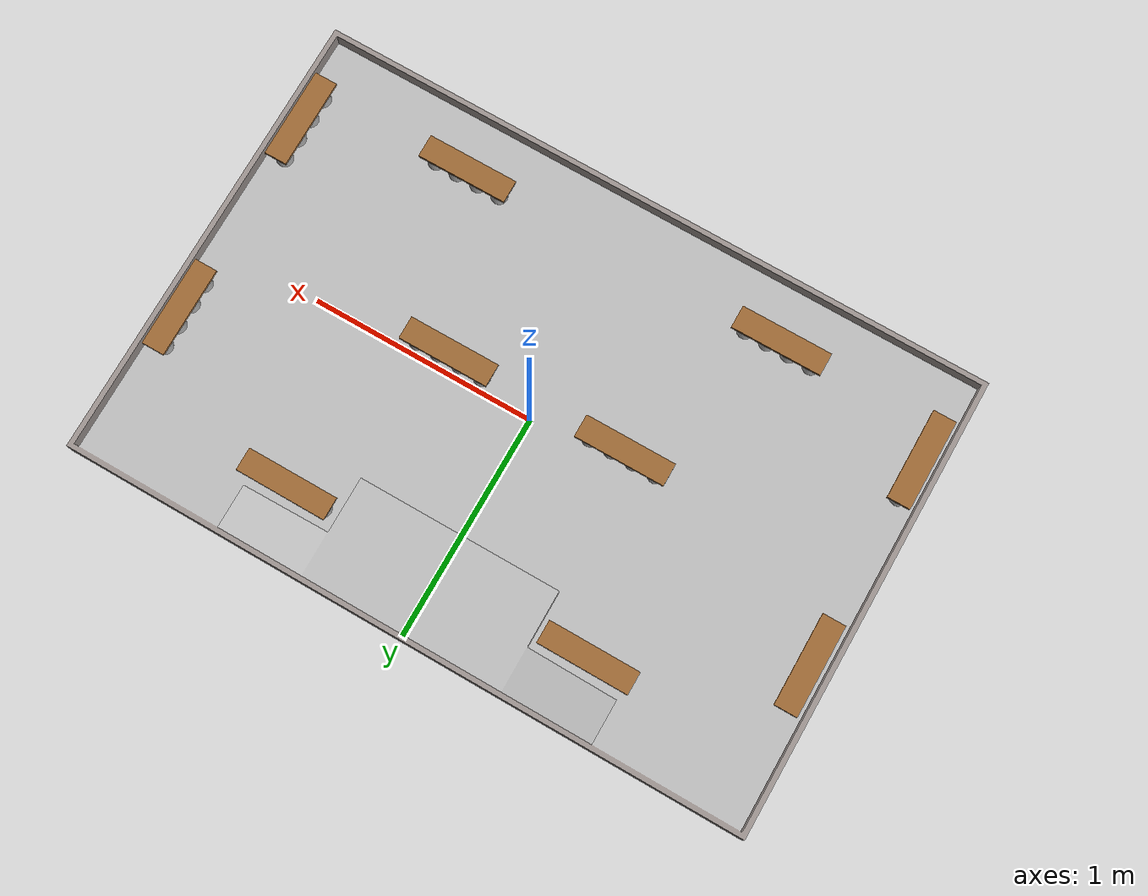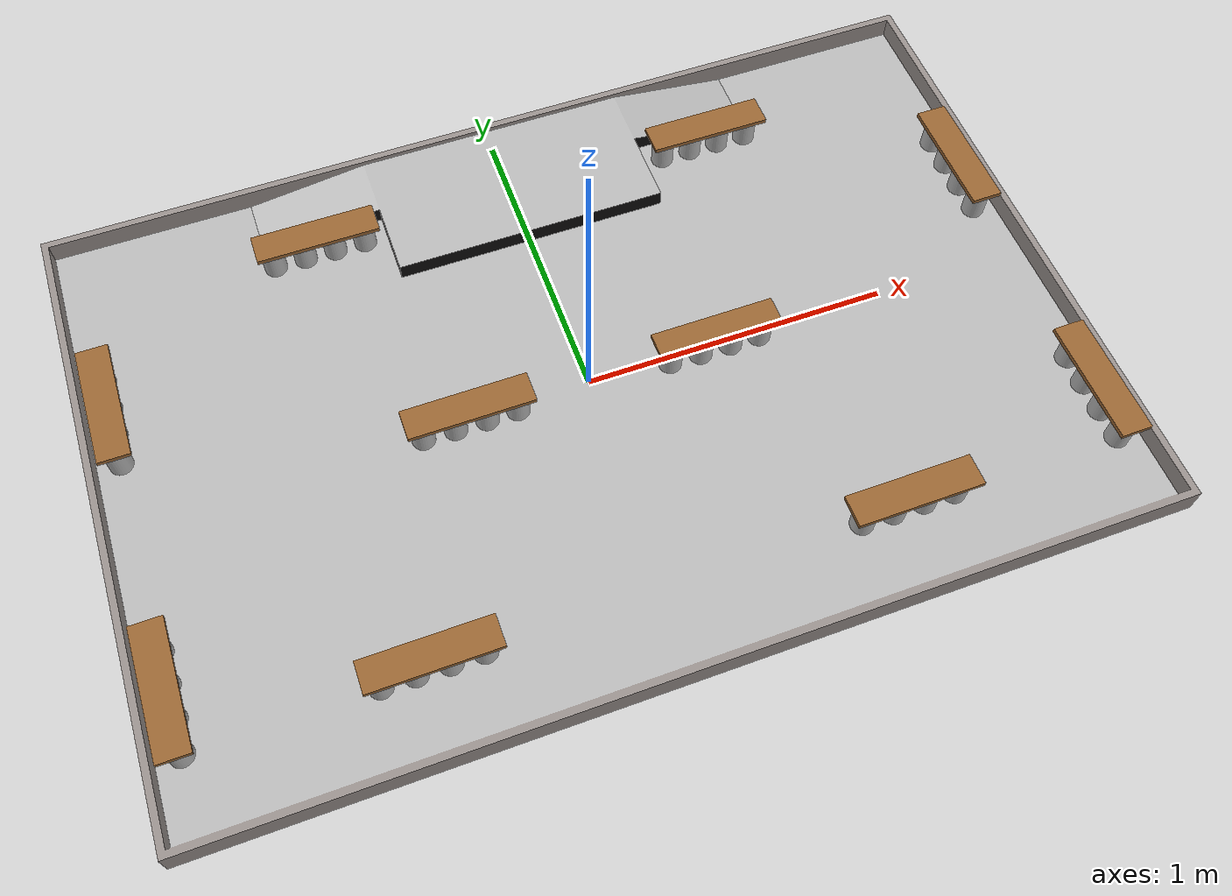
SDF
<sdf version="1.7">
 <world name="default">
  <gravity>0 0 -9.8</gravity>
  <magnetic_field>6e-06 2.3e-05 -4.2e-05</magnetic_field>
  <atmosphere type="adiabatic"/>
  <physics type="ode">
   <max_step_size>0.001</max_step_size>
   <real_time_factor>1</real_time_factor>
   <real_time_update_rate>1000</real_time_update_rate>
  </physics>
  <scene><ambient>1 1 1 1</ambient><background>0.7 0.7 0.7 1</background><shadows>0</shadows></scene>
  <audio><device>default</device></audio>
  <spherical_coordinates>
   <surface_model>EARTH_WGS84</surface_model>
   <latitude_deg>0</latitude_deg>
   <longitude_deg>0</longitude_deg>
   <elevation>0</elevation>
   <heading_deg>0</heading_deg>
  </spherical_coordinates>
  <model name="Table2025">
   <static>1</static>
   <link name="table">
    <inertial>
     <mass>108.217</mass>
     <inertia>
      <ixx>42.128</ixx>
      <ixy>-4.25029e-14</ixy>
      <ixz>6.83557e-16</ixz>
      <iyy>90.1988</iyy>
      <iyz>0</iyz>
      <izz>132.268</izz>
     </inertia>
    </inertial>
    <collision name="table_collision">
     <geometry><mesh><scale>1 1 1</scale><uri>model://Table2025/meshes/Table2025.dae</uri></mesh></geometry>
    </collision>
    <visual name="table_visual">
     <geometry><mesh><scale>1 1 1</scale><uri>model://Table2025/meshes/Table2025.dae</uri></mesh></geometry>
    </visual>
   </link>
  </model>
  <light name="user_spot_light_0" type="spot">
   <pose>0.011267 -0.01519 1 0 -0 0</pose>
   <diffuse>0.5 0.5 0.5 1</diffuse>
   <specular>0.1 0.1 0.1 1</specular>
   <direction>0 0 -1</direction>
   <attenuation><range>20</range><constant>1.2</constant><linear>0</linear><quadratic>0</quadratic></attenuation>
   <cast_shadows>0</cast_shadows>
   <spot><inner_angle>0.6</inner_angle><outer_angle>1</outer_angle><falloff>1</falloff></spot>
  </light>
  <light name="user_spot_light_1" type="spot">
   <pose>1.5614 -0.961277 1 0 -0 0</pose>
   <diffuse>0.5 0.5 0.5 1</diffuse>
   <specular>0.1 0.1 0.1 1</specular>
   <direction>0 0 -1</direction>
   <attenuation><range>20</range><constant>1.2</constant><linear>0</linear><quadratic>0</quadratic></attenuation>
   <cast_shadows>0</cast_shadows>
   <spot><inner_angle>0.6</inner_angle><outer_angle>1</outer_angle><falloff>1</falloff></spot>
  </light>
  <model name="Stage">
   <static>1</static>
   <plugin name="gz::sim::systems::Label" filename="gz-sim-label-system"><label>11</label></plugin>
   <link name="link_0">
    <inertial>
     <pose>0 0 0.02 0 -0 0</pose>
     <mass>0.025</mass>
     <inertia><ixx>2.5e-05</ixx><ixy>0</ixy><ixz>0</ixz><iyy>2.5e-05</iyy><iyz>0</iyz><izz>8e-06</izz></inertia>
    </inertial>
    <visual name="visual">
     <geometry><mesh><uri>model://Stage/meshes/stage.dae</uri><scale>1 1 1</scale></mesh></geometry>
    </visual>
    <collision name="table_collision">
     <geometry><mesh><scale>1 1 1</scale><uri>model://Stage/meshes/stage.dae</uri></mesh></geometry>
    </collision>
   </link>
   <pose>-0.071315 0.782 0.047551 0 0 -1.57</pose>
  </model>
  <model name="Can">
   <static>0</static>
   <plugin name="gz::sim::systems::Label" filename="gz-sim-label-system"><label>11</label></plugin>
   <link name="link_0">
    <inertial>
     <pose>0 0 0.02 0 -0 0</pose>
     <mass>0.025</mass>
     <inertia><ixx>2.5e-05</ixx><ixy>0</ixy><ixz>0</ixz><iyy>2.5e-05</iyy><iyz>0</iyz><izz>8e-06</izz></inertia>
    </inertial>
    <visual name="visual">
     <geometry><mesh><uri>model://Can/meshes/can.dae</uri><scale>1 1 1</scale></mesh></geometry>
    </visual>
    <collision name="collision">
     <max_contacts>20</max_contacts>
     <pose>0 0 0.0545 0 -0 0</pose>
     <geometry><cylinder><radius>0.0365</radius><length>0.109</length></cylinder></geometry>
     <surface>
      <friction><ode><mu>0.9</mu><mu2>0.9</mu2></ode></friction>
      <contact>
       <ode>
        <soft_cfm>0</soft_cfm>
        <soft_erp>0.2</soft_erp>
        <kp>10</kp>
        <kd>1e+09</kd>
        <max_vel>0.01</max_vel>
        <min_depth>0.001</min_depth>
       </ode>
      </contact>
     </surface>
    </collision>
   </link>
   <pose>-1.42534 0.474681 0.047323 -2.2e-05 8.2e-05 -0</pose>
  </model>
  <model name="Can_0">
   <static>0</static>
   <plugin name="gz::sim::systems::Label" filename="gz-sim-label-system"><label>11</label></plugin>
   <link name="link_0">
    <inertial>
     <pose>0 0 0.02 0 -0 0</pose>
     <mass>0.025</mass>
     <inertia><ixx>2.5e-05</ixx><ixy>0</ixy><ixz>0</ixz><iyy>2.5e-05</iyy><iyz>0</iyz><izz>8e-06</izz></inertia>
    </inertial>
    <visual name="visual">
     <geometry><mesh><uri>model://Can/meshes/can.dae</uri><scale>1 1 1</scale></mesh></geometry>
    </visual>
    <collision name="collision">
     <max_contacts>20</max_contacts>
     <pose>0 0 0.0545 0 -0 0</pose>
     <geometry><cylinder><radius>0.0365</radius><length>0.109</length></cylinder></geometry>
     <surface>
      <friction><ode><mu>0.9</mu><mu2>0.9</mu2></ode></friction>
      <contact>
       <ode>
        <soft_cfm>0</soft_cfm>
        <soft_erp>0.2</soft_erp>
        <kp>10</kp>
        <kd>1e+09</kd>
        <max_vel>0.01</max_vel>
        <min_depth>0.001</min_depth>
       </ode>
      </contact>
     </surface>
    </collision>
   </link>
   <pose>-1.42461 0.374855 0.047159 -2.4e-05 0.000124 1e-06</pose>
  </model>
  <model name="Can_1">
   <static>0</static>
   <plugin name="gz::sim::systems::Label" filename="gz-sim-label-system"><label>11</label></plugin>
   <link name="link_0">
    <inertial>
     <pose>0 0 0.02 0 -0 0</pose>
     <mass>0.025</mass>
     <inertia><ixx>2.5e-05</ixx><ixy>0</ixy><ixz>0</ixz><iyy>2.5e-05</iyy><iyz>0</iyz><izz>8e-06</izz></inertia>
    </inertial>
    <visual name="visual">
     <geometry><mesh><uri>model://Can/meshes/can.dae</uri><scale>1 1 1</scale></mesh></geometry>
    </visual>
    <collision name="collision">
     <max_contacts>20</max_contacts>
     <pose>0 0 0.0545 0 -0 0</pose>
     <geometry><cylinder><radius>0.0365</radius><length>0.109</length></cylinder></geometry>
     <surface>
      <friction><ode><mu>0.9</mu><mu2>0.9</mu2></ode></friction>
      <contact>
       <ode>
        <soft_cfm>0</soft_cfm>
        <soft_erp>0.2</soft_erp>
        <kp>10</kp>
        <kd>1e+09</kd>
        <max_vel>0.01</max_vel>
        <min_depth>0.001</min_depth>
       </ode>
      </contact>
     </surface>
    </collision>
   </link>
   <pose>-1.42486 0.27501 0.047584 -2.3e-05 0.000141 1e-06</pose>
  </model>
  <model name="Can_2">
   <static>0</static>
   <plugin name="gz::sim::systems::Label" filename="gz-sim-label-system"><label>11</label></plugin>
   <link name="link_0">
    <inertial>
     <pose>0 0 0.02 0 -0 0</pose>
     <mass>0.025</mass>
     <inertia><ixx>2.5e-05</ixx><ixy>0</ixy><ixz>0</ixz><iyy>2.5e-05</iyy><iyz>0</iyz><izz>8e-06</izz></inertia>
    </inertial>
    <visual name="visual">
     <geometry><mesh><uri>model://Can/meshes/can.dae</uri><scale>1 1 1</scale></mesh></geometry>
    </visual>
    <collision name="collision">
     <max_contacts>20</max_contacts>
     <pose>0 0 0.0545 0 -0 0</pose>
     <geometry><cylinder><radius>0.0365</radius><length>0.109</length></cylinder></geometry>
     <surface>
      <friction><ode><mu>0.9</mu><mu2>0.9</mu2></ode></friction>
      <contact>
       <ode>
        <soft_cfm>0</soft_cfm>
        <soft_erp>0.2</soft_erp>
        <kp>10</kp>
        <kd>1e+09</kd>
        <max_vel>0.01</max_vel>
        <min_depth>0.001</min_depth>
       </ode>
      </contact>
     </surface>
    </collision>
   </link>
   <pose>-1.42532 0.174907 0.046965 0 -0 0</pose>
  </model>
  <model name="Can_3">
   <static>0</static>
   <plugin name="gz::sim::systems::Label" filename="gz-sim-label-system"><label>11</label></plugin>
   <link name="link_0">
    <inertial>
     <pose>0 0 0.02 0 -0 0</pose>
     <mass>0.025</mass>
     <inertia><ixx>2.5e-05</ixx><ixy>0</ixy><ixz>0</ixz><iyy>2.5e-05</iyy><iyz>0</iyz><izz>8e-06</izz></inertia>
    </inertial>
    <visual name="visual">
     <geometry><mesh><uri>model://Can/meshes/can.dae</uri><scale>1 1 1</scale></mesh></geometry>
    </visual>
    <collision name="collision">
     <max_contacts>20</max_contacts>
     <pose>0 0 0.0545 0 -0 0</pose>
     <geometry><cylinder><radius>0.0365</radius><length>0.109</length></cylinder></geometry>
     <surface>
      <friction><ode><mu>0.9</mu><mu2>0.9</mu2></ode></friction>
      <contact>
       <ode>
        <soft_cfm>0</soft_cfm>
        <soft_erp>0.2</soft_erp>
        <kp>10</kp>
        <kd>1e+09</kd>
        <max_vel>0.01</max_vel>
        <min_depth>0.001</min_depth>
       </ode>
      </contact>
     </surface>
    </collision>
   </link>
   <pose>-1.42546 -0.750038 0.046914 0 -0 0</pose>
  </model>
  <model name="Can_4">
   <static>0</static>
   <plugin name="gz::sim::systems::Label" filename="gz-sim-label-system"><label>11</label></plugin>
   <link name="link_0">
    <inertial>
     <pose>0 0 0.02 0 -0 0</pose>
     <mass>0.025</mass>
     <inertia><ixx>2.5e-05</ixx><ixy>0</ixy><ixz>0</ixz><iyy>2.5e-05</iyy><iyz>0</iyz><izz>8e-06</izz></inertia>
    </inertial>
    <visual name="visual">
     <geometry><mesh><uri>model://Can/meshes/can.dae</uri><scale>1 1 1</scale></mesh></geometry>
    </visual>
    <collision name="collision">
     <max_contacts>20</max_contacts>
     <pose>0 0 0.0545 0 -0 0</pose>
     <geometry><cylinder><radius>0.0365</radius><length>0.109</length></cylinder></geometry>
     <surface>
      <friction><ode><mu>0.9</mu><mu2>0.9</mu2></ode></friction>
      <contact>
       <ode>
        <soft_cfm>0</soft_cfm>
        <soft_erp>0.2</soft_erp>
        <kp>10</kp>
        <kd>1e+09</kd>
        <max_vel>0.01</max_vel>
        <min_depth>0.001</min_depth>
       </ode>
      </contact>
     </surface>
    </collision>
   </link>
   <pose>-1.42553 -0.64996 0.047006 0.000123 0.000204 -1e-06</pose>
  </model>
  <model name="Can_5">
   <static>0</static>
   <plugin name="gz::sim::systems::Label" filename="gz-sim-label-system"><label>11</label></plugin>
   <link name="link_0">
    <inertial>
     <pose>0 0 0.02 0 -0 0</pose>
     <mass>0.025</mass>
     <inertia><ixx>2.5e-05</ixx><ixy>0</ixy><ixz>0</ixz><iyy>2.5e-05</iyy><iyz>0</iyz><izz>8e-06</izz></inertia>
    </inertial>
    <visual name="visual">
     <geometry><mesh><uri>model://Can/meshes/can.dae</uri><scale>1 1 1</scale></mesh></geometry>
    </visual>
    <collision name="collision">
     <max_contacts>20</max_contacts>
     <pose>0 0 0.0545 0 -0 0</pose>
     <geometry><cylinder><radius>0.0365</radius><length>0.109</length></cylinder></geometry>
     <surface>
      <friction><ode><mu>0.9</mu><mu2>0.9</mu2></ode></friction>
      <contact>
       <ode>
        <soft_cfm>0</soft_cfm>
        <soft_erp>0.2</soft_erp>
        <kp>10</kp>
        <kd>1e+09</kd>
        <max_vel>0.01</max_vel>
        <min_depth>0.001</min_depth>
       </ode>
      </contact>
     </surface>
    </collision>
   </link>
   <pose>-1.42525 -0.54997 0.047629 8.9e-05 0.000146 0</pose>
  </model>
  <model name="Can_6">
   <static>0</static>
   <plugin name="gz::sim::systems::Label" filename="gz-sim-label-system"><label>11</label></plugin>
   <link name="link_0">
    <inertial>
     <pose>0 0 0.02 0 -0 0</pose>
     <mass>0.025</mass>
     <inertia><ixx>2.5e-05</ixx><ixy>0</ixy><ixz>0</ixz><iyy>2.5e-05</iyy><iyz>0</iyz><izz>8e-06</izz></inertia>
    </inertial>
    <visual name="visual">
     <geometry><mesh><uri>model://Can/meshes/can.dae</uri><scale>1 1 1</scale></mesh></geometry>
    </visual>
    <collision name="collision">
     <max_contacts>20</max_contacts>
     <pose>0 0 0.0545 0 -0 0</pose>
     <geometry><cylinder><radius>0.0365</radius><length>0.109</length></cylinder></geometry>
     <surface>
      <friction><ode><mu>0.9</mu><mu2>0.9</mu2></ode></friction>
      <contact>
       <ode>
        <soft_cfm>0</soft_cfm>
        <soft_erp>0.2</soft_erp>
        <kp>10</kp>
        <kd>1e+09</kd>
        <max_vel>0.01</max_vel>
        <min_depth>0.001</min_depth>
       </ode>
      </contact>
     </surface>
    </collision>
   </link>
   <pose>-1.42518 -0.449827 0.047314 5e-06 2.1e-05 -0</pose>
  </model>
  <model name="Can_7">
   <static>0</static>
   <plugin name="gz::sim::systems::Label" filename="gz-sim-label-system"><label>11</label></plugin>
   <link name="link_0">
    <inertial>
     <pose>0 0 0.02 0 -0 0</pose>
     <mass>0.025</mass>
     <inertia><ixx>2.5e-05</ixx><ixy>0</ixy><ixz>0</ixz><iyy>2.5e-05</iyy><iyz>0</iyz><izz>8e-06</izz></inertia>
    </inertial>
    <visual name="visual">
     <geometry><mesh><uri>model://Can/meshes/can.dae</uri><scale>1 1 1</scale></mesh></geometry>
    </visual>
    <collision name="collision">
     <max_contacts>20</max_contacts>
     <pose>0 0 0.0545 0 -0 0</pose>
     <geometry><cylinder><radius>0.0365</radius><length>0.109</length></cylinder></geometry>
     <surface>
      <friction><ode><mu>0.9</mu><mu2>0.9</mu2></ode></friction>
      <contact>
       <ode>
        <soft_cfm>0</soft_cfm>
        <soft_erp>0.2</soft_erp>
        <kp>10</kp>
        <kd>1e+09</kd>
        <max_vel>0.01</max_vel>
        <min_depth>0.001</min_depth>
       </ode>
      </contact>
     </surface>
    </collision>
   </link>
   <pose>-0.825139 0.725605 0.047322 -0.000366 5.9e-05 0</pose>
  </model>
  <model name="Can_8">
   <static>0</static>
   <plugin name="gz::sim::systems::Label" filename="gz-sim-label-system"><label>11</label></plugin>
   <link name="link_0">
    <inertial>
     <pose>0 0 0.02 0 -0 0</pose>
     <mass>0.025</mass>
     <inertia><ixx>2.5e-05</ixx><ixy>0</ixy><ixz>0</ixz><iyy>2.5e-05</iyy><iyz>0</iyz><izz>8e-06</izz></inertia>
    </inertial>
    <visual name="visual">
     <geometry><mesh><uri>model://Can/meshes/can.dae</uri><scale>1 1 1</scale></mesh></geometry>
    </visual>
    <collision name="collision">
     <max_contacts>20</max_contacts>
     <pose>0 0 0.0545 0 -0 0</pose>
     <geometry><cylinder><radius>0.0365</radius><length>0.109</length></cylinder></geometry>
     <surface>
      <friction><ode><mu>0.9</mu><mu2>0.9</mu2></ode></friction>
      <contact>
       <ode>
        <soft_cfm>0</soft_cfm>
        <soft_erp>0.2</soft_erp>
        <kp>10</kp>
        <kd>1e+09</kd>
        <max_vel>0.01</max_vel>
        <min_depth>0.001</min_depth>
       </ode>
      </contact>
     </surface>
    </collision>
   </link>
   <pose>-0.724833 0.725455 0.047322 -0.000464 6.2e-05 -1e-06</pose>
  </model>
  <model name="Can_9">
   <static>0</static>
   <plugin name="gz::sim::systems::Label" filename="gz-sim-label-system"><label>11</label></plugin>
   <link name="link_0">
    <inertial>
     <pose>0 0 0.02 0 -0 0</pose>
     <mass>0.025</mass>
     <inertia><ixx>2.5e-05</ixx><ixy>0</ixy><ixz>0</ixz><iyy>2.5e-05</iyy><iyz>0</iyz><izz>8e-06</izz></inertia>
    </inertial>
    <visual name="visual">
     <geometry><mesh><uri>model://Can/meshes/can.dae</uri><scale>1 1 1</scale></mesh></geometry>
    </visual>
    <collision name="collision">
     <max_contacts>20</max_contacts>
     <pose>0 0 0.0545 0 -0 0</pose>
     <geometry><cylinder><radius>0.0365</radius><length>0.109</length></cylinder></geometry>
     <surface>
      <friction><ode><mu>0.9</mu><mu2>0.9</mu2></ode></friction>
      <contact>
       <ode>
        <soft_cfm>0</soft_cfm>
        <soft_erp>0.2</soft_erp>
        <kp>10</kp>
        <kd>1e+09</kd>
        <max_vel>0.01</max_vel>
        <min_depth>0.001</min_depth>
       </ode>
      </contact>
     </surface>
    </collision>
   </link>
   <pose>-0.624857 0.725021 0.047324 -0.000449 6.1e-05 0</pose>
  </model>
  <model name="Can_20">
   <static>0</static>
   <plugin name="gz::sim::systems::Label" filename="gz-sim-label-system"><label>11</label></plugin>
   <link name="link_0">
    <inertial>
     <pose>0 0 0.02 0 -0 0</pose>
     <mass>0.025</mass>
     <inertia><ixx>2.5e-05</ixx><ixy>0</ixy><ixz>0</ixz><iyy>2.5e-05</iyy><iyz>0</iyz><izz>8e-06</izz></inertia>
    </inertial>
    <visual name="visual">
     <geometry><mesh><uri>model://Can/meshes/can.dae</uri><scale>1 1 1</scale></mesh></geometry>
    </visual>
    <collision name="collision">
     <max_contacts>20</max_contacts>
     <pose>0 0 0.0545 0 -0 0</pose>
     <geometry><cylinder><radius>0.0365</radius><length>0.109</length></cylinder></geometry>
     <surface>
      <friction><ode><mu>0.9</mu><mu2>0.9</mu2></ode></friction>
      <contact>
       <ode>
        <soft_cfm>0</soft_cfm>
        <soft_erp>0.2</soft_erp>
        <kp>10</kp>
        <kd>1e+09</kd>
        <max_vel>0.01</max_vel>
        <min_depth>0.001</min_depth>
       </ode>
      </contact>
     </surface>
    </collision>
   </link>
   <pose>-0.524849 0.725291 0.047322 -0.000333 4.1e-05 0</pose>
  </model>
  <model name="Can_31">
   <static>0</static>
   <plugin name="gz::sim::systems::Label" filename="gz-sim-label-system"><label>11</label></plugin>
   <link name="link_0">
    <inertial>
     <pose>0 0 0.02 0 -0 0</pose>
     <mass>0.025</mass>
     <inertia><ixx>2.5e-05</ixx><ixy>0</ixy><ixz>0</ixz><iyy>2.5e-05</iyy><iyz>0</iyz><izz>8e-06</izz></inertia>
    </inertial>
    <visual name="visual">
     <geometry><mesh><uri>model://Can/meshes/can.dae</uri><scale>1 1 1</scale></mesh></geometry>
    </visual>
    <collision name="collision">
     <max_contacts>20</max_contacts>
     <pose>0 0 0.0545 0 -0 0</pose>
     <geometry><cylinder><radius>0.0365</radius><length>0.109</length></cylinder></geometry>
     <surface>
      <friction><ode><mu>0.9</mu><mu2>0.9</mu2></ode></friction>
      <contact>
       <ode>
        <soft_cfm>0</soft_cfm>
        <soft_erp>0.2</soft_erp>
        <kp>10</kp>
        <kd>1e+09</kd>
        <max_vel>0.01</max_vel>
        <min_depth>0.001</min_depth>
       </ode>
      </contact>
     </surface>
    </collision>
   </link>
   <pose>0.524631 0.725786 0.047323 -3.6e-05 5.5e-05 0</pose>
  </model>
  <model name="Can_33">
   <static>0</static>
   <plugin name="gz::sim::systems::Label" filename="gz-sim-label-system"><label>11</label></plugin>
   <link name="link_0">
    <inertial>
     <pose>0 0 0.02 0 -0 0</pose>
     <mass>0.025</mass>
     <inertia><ixx>2.5e-05</ixx><ixy>0</ixy><ixz>0</ixz><iyy>2.5e-05</iyy><iyz>0</iyz><izz>8e-06</izz></inertia>
    </inertial>
    <visual name="visual">
     <geometry><mesh><uri>model://Can/meshes/can.dae</uri><scale>1 1 1</scale></mesh></geometry>
    </visual>
    <collision name="collision">
     <max_contacts>20</max_contacts>
     <pose>0 0 0.0545 0 -0 0</pose>
     <geometry><cylinder><radius>0.0365</radius><length>0.109</length></cylinder></geometry>
     <surface>
      <friction><ode><mu>0.9</mu><mu2>0.9</mu2></ode></friction>
      <contact>
       <ode>
        <soft_cfm>0</soft_cfm>
        <soft_erp>0.2</soft_erp>
        <kp>10</kp>
        <kd>1e+09</kd>
        <max_vel>0.01</max_vel>
        <min_depth>0.001</min_depth>
       </ode>
      </contact>
     </surface>
    </collision>
   </link>
   <pose>0.625282 0.726048 0.047322 -4.3e-05 5.6e-05 0</pose>
  </model>
  <model name="Can_34">
   <static>0</static>
   <plugin name="gz::sim::systems::Label" filename="gz-sim-label-system"><label>11</label></plugin>
   <link name="link_0">
    <inertial>
     <pose>0 0 0.02 0 -0 0</pose>
     <mass>0.025</mass>
     <inertia><ixx>2.5e-05</ixx><ixy>0</ixy><ixz>0</ixz><iyy>2.5e-05</iyy><iyz>0</iyz><izz>8e-06</izz></inertia>
    </inertial>
    <visual name="visual">
     <geometry><mesh><uri>model://Can/meshes/can.dae</uri><scale>1 1 1</scale></mesh></geometry>
    </visual>
    <collision name="collision">
     <max_contacts>20</max_contacts>
     <pose>0 0 0.0545 0 -0 0</pose>
     <geometry><cylinder><radius>0.0365</radius><length>0.109</length></cylinder></geometry>
     <surface>
      <friction><ode><mu>0.9</mu><mu2>0.9</mu2></ode></friction>
      <contact>
       <ode>
        <soft_cfm>0</soft_cfm>
        <soft_erp>0.2</soft_erp>
        <kp>10</kp>
        <kd>1e+09</kd>
        <max_vel>0.01</max_vel>
        <min_depth>0.001</min_depth>
       </ode>
      </contact>
     </surface>
    </collision>
   </link>
   <pose>0.72493 0.725553 0.047324 -2.9e-05 5.7e-05 0</pose>
  </model>
  <model name="Can_35">
   <static>0</static>
   <plugin name="gz::sim::systems::Label" filename="gz-sim-label-system"><label>11</label></plugin>
   <link name="link_0">
    <inertial>
     <pose>0 0 0.02 0 -0 0</pose>
     <mass>0.025</mass>
     <inertia><ixx>2.5e-05</ixx><ixy>0</ixy><ixz>0</ixz><iyy>2.5e-05</iyy><iyz>0</iyz><izz>8e-06</izz></inertia>
    </inertial>
    <visual name="visual">
     <geometry><mesh><uri>model://Can/meshes/can.dae</uri><scale>1 1 1</scale></mesh></geometry>
    </visual>
    <collision name="collision">
     <max_contacts>20</max_contacts>
     <pose>0 0 0.0545 0 -0 0</pose>
     <geometry><cylinder><radius>0.0365</radius><length>0.109</length></cylinder></geometry>
     <surface>
      <friction><ode><mu>0.9</mu><mu2>0.9</mu2></ode></friction>
      <contact>
       <ode>
        <soft_cfm>0</soft_cfm>
        <soft_erp>0.2</soft_erp>
        <kp>10</kp>
        <kd>1e+09</kd>
        <max_vel>0.01</max_vel>
        <min_depth>0.001</min_depth>
       </ode>
      </contact>
     </surface>
    </collision>
   </link>
   <pose>0.825085 0.725093 0.047323 -2e-05 5.4e-05 0</pose>
  </model>
  <model name="Can_36">
   <static>0</static>
   <plugin name="gz::sim::systems::Label" filename="gz-sim-label-system"><label>11</label></plugin>
   <link name="link_0">
    <inertial>
     <pose>0 0 0.02 0 -0 0</pose>
     <mass>0.025</mass>
     <inertia><ixx>2.5e-05</ixx><ixy>0</ixy><ixz>0</ixz><iyy>2.5e-05</iyy><iyz>0</iyz><izz>8e-06</izz></inertia>
    </inertial>
    <visual name="visual">
     <geometry><mesh><uri>model://Can/meshes/can.dae</uri><scale>1 1 1</scale></mesh></geometry>
    </visual>
    <collision name="collision">
     <max_contacts>20</max_contacts>
     <pose>0 0 0.0545 0 -0 0</pose>
     <geometry><cylinder><radius>0.0365</radius><length>0.109</length></cylinder></geometry>
     <surface>
      <friction><ode><mu>0.9</mu><mu2>0.9</mu2></ode></friction>
      <contact>
       <ode>
        <soft_cfm>0</soft_cfm>
        <soft_erp>0.2</soft_erp>
        <kp>10</kp>
        <kd>1e+09</kd>
        <max_vel>0.01</max_vel>
        <min_depth>0.001</min_depth>
       </ode>
      </contact>
     </surface>
    </collision>
   </link>
   <pose>1.42524 0.475414 0.047322 -0.000246 0.000298 0</pose>
  </model>
  <model name="Can_37">
   <static>0</static>
   <plugin name="gz::sim::systems::Label" filename="gz-sim-label-system"><label>11</label></plugin>
   <link name="link_0">
    <inertial>
     <pose>0 0 0.02 0 -0 0</pose>
     <mass>0.025</mass>
     <inertia><ixx>2.5e-05</ixx><ixy>0</ixy><ixz>0</ixz><iyy>2.5e-05</iyy><iyz>0</iyz><izz>8e-06</izz></inertia>
    </inertial>
    <visual name="visual">
     <geometry><mesh><uri>model://Can/meshes/can.dae</uri><scale>1 1 1</scale></mesh></geometry>
    </visual>
    <collision name="collision">
     <max_contacts>20</max_contacts>
     <pose>0 0 0.0545 0 -0 0</pose>
     <geometry><cylinder><radius>0.0365</radius><length>0.109</length></cylinder></geometry>
     <surface>
      <friction><ode><mu>0.9</mu><mu2>0.9</mu2></ode></friction>
      <contact>
       <ode>
        <soft_cfm>0</soft_cfm>
        <soft_erp>0.2</soft_erp>
        <kp>10</kp>
        <kd>1e+09</kd>
        <max_vel>0.01</max_vel>
        <min_depth>0.001</min_depth>
       </ode>
      </contact>
     </surface>
    </collision>
   </link>
   <pose>1.42521 0.375005 0.047323 -0.000219 0.000711 3e-06</pose>
  </model>
  <model name="Can_38">
   <static>0</static>
   <plugin name="gz::sim::systems::Label" filename="gz-sim-label-system"><label>11</label></plugin>
   <link name="link_0">
    <inertial>
     <pose>0 0 0.02 0 -0 0</pose>
     <mass>0.025</mass>
     <inertia><ixx>2.5e-05</ixx><ixy>0</ixy><ixz>0</ixz><iyy>2.5e-05</iyy><iyz>0</iyz><izz>8e-06</izz></inertia>
    </inertial>
    <visual name="visual">
     <geometry><mesh><uri>model://Can/meshes/can.dae</uri><scale>1 1 1</scale></mesh></geometry>
    </visual>
    <collision name="collision">
     <max_contacts>20</max_contacts>
     <pose>0 0 0.0545 0 -0 0</pose>
     <geometry><cylinder><radius>0.0365</radius><length>0.109</length></cylinder></geometry>
     <surface>
      <friction><ode><mu>0.9</mu><mu2>0.9</mu2></ode></friction>
      <contact>
       <ode>
        <soft_cfm>0</soft_cfm>
        <soft_erp>0.2</soft_erp>
        <kp>10</kp>
        <kd>1e+09</kd>
        <max_vel>0.01</max_vel>
        <min_depth>0.001</min_depth>
       </ode>
      </contact>
     </surface>
    </collision>
   </link>
   <pose>1.42548 0.274974 0.047329 0.000549 0.000614 6e-06</pose>
  </model>
  <model name="Can_10">
   <static>0</static>
   <plugin name="gz::sim::systems::Label" filename="gz-sim-label-system"><label>11</label></plugin>
   <link name="link_0">
    <inertial>
     <pose>0 0 0.02 0 -0 0</pose>
     <mass>0.025</mass>
     <inertia><ixx>2.5e-05</ixx><ixy>0</ixy><ixz>0</ixz><iyy>2.5e-05</iyy><iyz>0</iyz><izz>8e-06</izz></inertia>
    </inertial>
    <visual name="visual">
     <geometry><mesh><uri>model://Can/meshes/can.dae</uri><scale>1 1 1</scale></mesh></geometry>
    </visual>
    <collision name="collision">
     <max_contacts>20</max_contacts>
     <pose>0 0 0.0545 0 -0 0</pose>
     <geometry><cylinder><radius>0.0365</radius><length>0.109</length></cylinder></geometry>
     <surface>
      <friction><ode><mu>0.9</mu><mu2>0.9</mu2></ode></friction>
      <contact>
       <ode>
        <soft_cfm>0</soft_cfm>
        <soft_erp>0.2</soft_erp>
        <kp>10</kp>
        <kd>1e+09</kd>
        <max_vel>0.01</max_vel>
        <min_depth>0.001</min_depth>
       </ode>
      </contact>
     </surface>
    </collision>
   </link>
   <pose>1.42613 0.174484 0.047323 0 -0 0</pose>
  </model>
  <model name="Can_11">
   <static>0</static>
   <plugin name="gz::sim::systems::Label" filename="gz-sim-label-system"><label>11</label></plugin>
   <link name="link_0">
    <inertial>
     <pose>0 0 0.02 0 -0 0</pose>
     <mass>0.025</mass>
     <inertia><ixx>2.5e-05</ixx><ixy>0</ixy><ixz>0</ixz><iyy>2.5e-05</iyy><iyz>0</iyz><izz>8e-06</izz></inertia>
    </inertial>
    <visual name="visual">
     <geometry><mesh><uri>model://Can/meshes/can.dae</uri><scale>1 1 1</scale></mesh></geometry>
    </visual>
    <collision name="collision">
     <max_contacts>20</max_contacts>
     <pose>0 0 0.0545 0 -0 0</pose>
     <geometry><cylinder><radius>0.0365</radius><length>0.109</length></cylinder></geometry>
     <surface>
      <friction><ode><mu>0.9</mu><mu2>0.9</mu2></ode></friction>
      <contact>
       <ode>
        <soft_cfm>0</soft_cfm>
        <soft_erp>0.2</soft_erp>
        <kp>10</kp>
        <kd>1e+09</kd>
        <max_vel>0.01</max_vel>
        <min_depth>0.001</min_depth>
       </ode>
      </contact>
     </surface>
    </collision>
   </link>
   <pose>1.4255 -0.449936 0.047322 -0.00011 0.00019 0</pose>
  </model>
  <model name="Can_12">
   <static>0</static>
   <plugin name="gz::sim::systems::Label" filename="gz-sim-label-system"><label>11</label></plugin>
   <link name="link_0">
    <inertial>
     <pose>0 0 0.02 0 -0 0</pose>
     <mass>0.025</mass>
     <inertia><ixx>2.5e-05</ixx><ixy>0</ixy><ixz>0</ixz><iyy>2.5e-05</iyy><iyz>0</iyz><izz>8e-06</izz></inertia>
    </inertial>
    <visual name="visual">
     <geometry><mesh><uri>model://Can/meshes/can.dae</uri><scale>1 1 1</scale></mesh></geometry>
    </visual>
    <collision name="collision">
     <max_contacts>20</max_contacts>
     <pose>0 0 0.0545 0 -0 0</pose>
     <geometry><cylinder><radius>0.0365</radius><length>0.109</length></cylinder></geometry>
     <surface>
      <friction><ode><mu>0.9</mu><mu2>0.9</mu2></ode></friction>
      <contact>
       <ode>
        <soft_cfm>0</soft_cfm>
        <soft_erp>0.2</soft_erp>
        <kp>10</kp>
        <kd>1e+09</kd>
        <max_vel>0.01</max_vel>
        <min_depth>0.001</min_depth>
       </ode>
      </contact>
     </surface>
    </collision>
   </link>
   <pose>1.42505 -0.550146 0.047323 -0.000122 0.000419 2e-06</pose>
  </model>
  <model name="Can_13">
   <static>0</static>
   <plugin name="gz::sim::systems::Label" filename="gz-sim-label-system"><label>11</label></plugin>
   <link name="link_0">
    <inertial>
     <pose>0 0 0.02 0 -0 0</pose>
     <mass>0.025</mass>
     <inertia><ixx>2.5e-05</ixx><ixy>0</ixy><ixz>0</ixz><iyy>2.5e-05</iyy><iyz>0</iyz><izz>8e-06</izz></inertia>
    </inertial>
    <visual name="visual">
     <geometry><mesh><uri>model://Can/meshes/can.dae</uri><scale>1 1 1</scale></mesh></geometry>
    </visual>
    <collision name="collision">
     <max_contacts>20</max_contacts>
     <pose>0 0 0.0545 0 -0 0</pose>
     <geometry><cylinder><radius>0.0365</radius><length>0.109</length></cylinder></geometry>
     <surface>
      <friction><ode><mu>0.9</mu><mu2>0.9</mu2></ode></friction>
      <contact>
       <ode>
        <soft_cfm>0</soft_cfm>
        <soft_erp>0.2</soft_erp>
        <kp>10</kp>
        <kd>1e+09</kd>
        <max_vel>0.01</max_vel>
        <min_depth>0.001</min_depth>
       </ode>
      </contact>
     </surface>
    </collision>
   </link>
   <pose>1.42525 -0.649943 0.047323 -0.000126 0.000479 1e-06</pose>
  </model>
  <model name="Can_14">
   <static>0</static>
   <plugin name="gz::sim::systems::Label" filename="gz-sim-label-system"><label>11</label></plugin>
   <link name="link_0">
    <inertial>
     <pose>0 0 0.02 0 -0 0</pose>
     <mass>0.025</mass>
     <inertia><ixx>2.5e-05</ixx><ixy>0</ixy><ixz>0</ixz><iyy>2.5e-05</iyy><iyz>0</iyz><izz>8e-06</izz></inertia>
    </inertial>
    <visual name="visual">
     <geometry><mesh><uri>model://Can/meshes/can.dae</uri><scale>1 1 1</scale></mesh></geometry>
    </visual>
    <collision name="collision">
     <max_contacts>20</max_contacts>
     <pose>0 0 0.0545 0 -0 0</pose>
     <geometry><cylinder><radius>0.0365</radius><length>0.109</length></cylinder></geometry>
     <surface>
      <friction><ode><mu>0.9</mu><mu2>0.9</mu2></ode></friction>
      <contact>
       <ode>
        <soft_cfm>0</soft_cfm>
        <soft_erp>0.2</soft_erp>
        <kp>10</kp>
        <kd>1e+09</kd>
        <max_vel>0.01</max_vel>
        <min_depth>0.001</min_depth>
       </ode>
      </contact>
     </surface>
    </collision>
   </link>
   <pose>1.42505 -0.75008 0.047323 0 -0 0</pose>
  </model>
  <model name="Can_15">
   <static>0</static>
   <plugin name="gz::sim::systems::Label" filename="gz-sim-label-system"><label>11</label></plugin>
   <link name="link_0">
    <inertial>
     <pose>0 0 0.02 0 -0 0</pose>
     <mass>0.025</mass>
     <inertia><ixx>2.5e-05</ixx><ixy>0</ixy><ixz>0</ixz><iyy>2.5e-05</iyy><iyz>0</iyz><izz>8e-06</izz></inertia>
    </inertial>
    <visual name="visual">
     <geometry><mesh><uri>model://Can/meshes/can.dae</uri><scale>1 1 1</scale></mesh></geometry>
    </visual>
    <collision name="collision">
     <max_contacts>20</max_contacts>
     <pose>0 0 0.0545 0 -0 0</pose>
     <geometry><cylinder><radius>0.0365</radius><length>0.109</length></cylinder></geometry>
     <surface>
      <friction><ode><mu>0.9</mu><mu2>0.9</mu2></ode></friction>
      <contact>
       <ode>
        <soft_cfm>0</soft_cfm>
        <soft_erp>0.2</soft_erp>
        <kp>10</kp>
        <kd>1e+09</kd>
        <max_vel>0.01</max_vel>
        <min_depth>0.001</min_depth>
       </ode>
      </contact>
     </surface>
    </collision>
   </link>
   <pose>0.249592 -0.049779 0.047325 -4.4e-05 -3.4e-05 0</pose>
  </model>
  <model name="Can_16">
   <static>0</static>
   <plugin name="gz::sim::systems::Label" filename="gz-sim-label-system"><label>11</label></plugin>
   <link name="link_0">
    <inertial>
     <pose>0 0 0.02 0 -0 0</pose>
     <mass>0.025</mass>
     <inertia><ixx>2.5e-05</ixx><ixy>0</ixy><ixz>0</ixz><iyy>2.5e-05</iyy><iyz>0</iyz><izz>8e-06</izz></inertia>
    </inertial>
    <visual name="visual">
     <geometry><mesh><uri>model://Can/meshes/can.dae</uri><scale>1 1 1</scale></mesh></geometry>
    </visual>
    <collision name="collision">
     <max_contacts>20</max_contacts>
     <pose>0 0 0.0545 0 -0 0</pose>
     <geometry><cylinder><radius>0.0365</radius><length>0.109</length></cylinder></geometry>
     <surface>
      <friction><ode><mu>0.9</mu><mu2>0.9</mu2></ode></friction>
      <contact>
       <ode>
        <soft_cfm>0</soft_cfm>
        <soft_erp>0.2</soft_erp>
        <kp>10</kp>
        <kd>1e+09</kd>
        <max_vel>0.01</max_vel>
        <min_depth>0.001</min_depth>
       </ode>
      </contact>
     </surface>
    </collision>
   </link>
   <pose>0.351194 -0.051121 0.047327 0.000565 2.5e-05 4e-06</pose>
  </model>
  <model name="Can_17">
   <static>0</static>
   <plugin name="gz::sim::systems::Label" filename="gz-sim-label-system"><label>11</label></plugin>
   <link name="link_0">
    <inertial>
     <pose>0 0 0.02 0 -0 0</pose>
     <mass>0.025</mass>
     <inertia><ixx>2.5e-05</ixx><ixy>0</ixy><ixz>0</ixz><iyy>2.5e-05</iyy><iyz>0</iyz><izz>8e-06</izz></inertia>
    </inertial>
    <visual name="visual">
     <geometry><mesh><uri>model://Can/meshes/can.dae</uri><scale>1 1 1</scale></mesh></geometry>
    </visual>
    <collision name="collision">
     <max_contacts>20</max_contacts>
     <pose>0 0 0.0545 0 -0 0</pose>
     <geometry><cylinder><radius>0.0365</radius><length>0.109</length></cylinder></geometry>
     <surface>
      <friction><ode><mu>0.9</mu><mu2>0.9</mu2></ode></friction>
      <contact>
       <ode>
        <soft_cfm>0</soft_cfm>
        <soft_erp>0.2</soft_erp>
        <kp>10</kp>
        <kd>1e+09</kd>
        <max_vel>0.01</max_vel>
        <min_depth>0.001</min_depth>
       </ode>
      </contact>
     </surface>
    </collision>
   </link>
   <pose>0.451754 -0.050976 0.047323 0.000482 2.8e-05 2e-06</pose>
  </model>
  <model name="Can_18">
   <static>0</static>
   <plugin name="gz::sim::systems::Label" filename="gz-sim-label-system"><label>11</label></plugin>
   <link name="link_0">
    <inertial>
     <pose>0 0 0.02 0 -0 0</pose>
     <mass>0.025</mass>
     <inertia><ixx>2.5e-05</ixx><ixy>0</ixy><ixz>0</ixz><iyy>2.5e-05</iyy><iyz>0</iyz><izz>8e-06</izz></inertia>
    </inertial>
    <visual name="visual">
     <geometry><mesh><uri>model://Can/meshes/can.dae</uri><scale>1 1 1</scale></mesh></geometry>
    </visual>
    <collision name="collision">
     <max_contacts>20</max_contacts>
     <pose>0 0 0.0545 0 -0 0</pose>
     <geometry><cylinder><radius>0.0365</radius><length>0.109</length></cylinder></geometry>
     <surface>
      <friction><ode><mu>0.9</mu><mu2>0.9</mu2></ode></friction>
      <contact>
       <ode>
        <soft_cfm>0</soft_cfm>
        <soft_erp>0.2</soft_erp>
        <kp>10</kp>
        <kd>1e+09</kd>
        <max_vel>0.01</max_vel>
        <min_depth>0.001</min_depth>
       </ode>
      </contact>
     </surface>
    </collision>
   </link>
   <pose>0.549782 -0.049608 0.047323 0.000268 2.1e-05 0</pose>
  </model>
  <model name="Can_19">
   <static>0</static>
   <plugin name="gz::sim::systems::Label" filename="gz-sim-label-system"><label>11</label></plugin>
   <link name="link_0">
    <inertial>
     <pose>0 0 0.02 0 -0 0</pose>
     <mass>0.025</mass>
     <inertia><ixx>2.5e-05</ixx><ixy>0</ixy><ixz>0</ixz><iyy>2.5e-05</iyy><iyz>0</iyz><izz>8e-06</izz></inertia>
    </inertial>
    <visual name="visual">
     <geometry><mesh><uri>model://Can/meshes/can.dae</uri><scale>1 1 1</scale></mesh></geometry>
    </visual>
    <collision name="collision">
     <max_contacts>20</max_contacts>
     <pose>0 0 0.0545 0 -0 0</pose>
     <geometry><cylinder><radius>0.0365</radius><length>0.109</length></cylinder></geometry>
     <surface>
      <friction><ode><mu>0.9</mu><mu2>0.9</mu2></ode></friction>
      <contact>
       <ode>
        <soft_cfm>0</soft_cfm>
        <soft_erp>0.2</soft_erp>
        <kp>10</kp>
        <kd>1e+09</kd>
        <max_vel>0.01</max_vel>
        <min_depth>0.001</min_depth>
       </ode>
      </contact>
     </surface>
    </collision>
   </link>
   <pose>-0.550319 -0.04974 0.047324 0.00019 -1.1e-05 0</pose>
  </model>
  <model name="Can_21">
   <static>0</static>
   <plugin name="gz::sim::systems::Label" filename="gz-sim-label-system"><label>11</label></plugin>
   <link name="link_0">
    <inertial>
     <pose>0 0 0.02 0 -0 0</pose>
     <mass>0.025</mass>
     <inertia><ixx>2.5e-05</ixx><ixy>0</ixy><ixz>0</ixz><iyy>2.5e-05</iyy><iyz>0</iyz><izz>8e-06</izz></inertia>
    </inertial>
    <visual name="visual">
     <geometry><mesh><uri>model://Can/meshes/can.dae</uri><scale>1 1 1</scale></mesh></geometry>
    </visual>
    <collision name="collision">
     <max_contacts>20</max_contacts>
     <pose>0 0 0.0545 0 -0 0</pose>
     <geometry><cylinder><radius>0.0365</radius><length>0.109</length></cylinder></geometry>
     <surface>
      <friction><ode><mu>0.9</mu><mu2>0.9</mu2></ode></friction>
      <contact>
       <ode>
        <soft_cfm>0</soft_cfm>
        <soft_erp>0.2</soft_erp>
        <kp>10</kp>
        <kd>1e+09</kd>
        <max_vel>0.01</max_vel>
        <min_depth>0.001</min_depth>
       </ode>
      </contact>
     </surface>
    </collision>
   </link>
   <pose>-0.449206 -0.050984 0.047326 0.000333 -1e-05 0</pose>
  </model>
  <model name="Can_22">
   <static>0</static>
   <plugin name="gz::sim::systems::Label" filename="gz-sim-label-system"><label>11</label></plugin>
   <link name="link_0">
    <inertial>
     <pose>0 0 0.02 0 -0 0</pose>
     <mass>0.025</mass>
     <inertia><ixx>2.5e-05</ixx><ixy>0</ixy><ixz>0</ixz><iyy>2.5e-05</iyy><iyz>0</iyz><izz>8e-06</izz></inertia>
    </inertial>
    <visual name="visual">
     <geometry><mesh><uri>model://Can/meshes/can.dae</uri><scale>1 1 1</scale></mesh></geometry>
    </visual>
    <collision name="collision">
     <max_contacts>20</max_contacts>
     <pose>0 0 0.0545 0 -0 0</pose>
     <geometry><cylinder><radius>0.0365</radius><length>0.109</length></cylinder></geometry>
     <surface>
      <friction><ode><mu>0.9</mu><mu2>0.9</mu2></ode></friction>
      <contact>
       <ode>
        <soft_cfm>0</soft_cfm>
        <soft_erp>0.2</soft_erp>
        <kp>10</kp>
        <kd>1e+09</kd>
        <max_vel>0.01</max_vel>
        <min_depth>0.001</min_depth>
       </ode>
      </contact>
     </surface>
    </collision>
   </link>
   <pose>-0.348793 -0.050871 0.047324 0.000329 -9e-06 -0</pose>
  </model>
  <model name="Can_23">
   <static>0</static>
   <plugin name="gz::sim::systems::Label" filename="gz-sim-label-system"><label>11</label></plugin>
   <link name="link_0">
    <inertial>
     <pose>0 0 0.02 0 -0 0</pose>
     <mass>0.025</mass>
     <inertia><ixx>2.5e-05</ixx><ixy>0</ixy><ixz>0</ixz><iyy>2.5e-05</iyy><iyz>0</iyz><izz>8e-06</izz></inertia>
    </inertial>
    <visual name="visual">
     <geometry><mesh><uri>model://Can/meshes/can.dae</uri><scale>1 1 1</scale></mesh></geometry>
    </visual>
    <collision name="collision">
     <max_contacts>20</max_contacts>
     <pose>0 0 0.0545 0 -0 0</pose>
     <geometry><cylinder><radius>0.0365</radius><length>0.109</length></cylinder></geometry>
     <surface>
      <friction><ode><mu>0.9</mu><mu2>0.9</mu2></ode></friction>
      <contact>
       <ode>
        <soft_cfm>0</soft_cfm>
        <soft_erp>0.2</soft_erp>
        <kp>10</kp>
        <kd>1e+09</kd>
        <max_vel>0.01</max_vel>
        <min_depth>0.001</min_depth>
       </ode>
      </contact>
     </surface>
    </collision>
   </link>
   <pose>-0.250116 -0.049773 0.047324 0.000194 -1.1e-05 0</pose>
  </model>
  <model name="Can_24">
   <static>0</static>
   <plugin name="gz::sim::systems::Label" filename="gz-sim-label-system"><label>11</label></plugin>
   <link name="link_0">
    <inertial>
     <pose>0 0 0.02 0 -0 0</pose>
     <mass>0.025</mass>
     <inertia><ixx>2.5e-05</ixx><ixy>0</ixy><ixz>0</ixz><iyy>2.5e-05</iyy><iyz>0</iyz><izz>8e-06</izz></inertia>
    </inertial>
    <visual name="visual">
     <geometry><mesh><uri>model://Can/meshes/can.dae</uri><scale>1 1 1</scale></mesh></geometry>
    </visual>
    <collision name="collision">
     <max_contacts>20</max_contacts>
     <pose>0 0 0.0545 0 -0 0</pose>
     <geometry><cylinder><radius>0.0365</radius><length>0.109</length></cylinder></geometry>
     <surface>
      <friction><ode><mu>0.9</mu><mu2>0.9</mu2></ode></friction>
      <contact>
       <ode>
        <soft_cfm>0</soft_cfm>
        <soft_erp>0.2</soft_erp>
        <kp>10</kp>
        <kd>1e+09</kd>
        <max_vel>0.01</max_vel>
        <min_depth>0.001</min_depth>
       </ode>
      </contact>
     </surface>
    </collision>
   </link>
   <pose>-0.575106 -0.750403 0.047368 -0.007696 0.003349 0.000203</pose>
  </model>
  <model name="Can_25">
   <static>0</static>
   <plugin name="gz::sim::systems::Label" filename="gz-sim-label-system"><label>11</label></plugin>
   <link name="link_0">
    <inertial>
     <pose>0 0 0.02 0 -0 0</pose>
     <mass>0.025</mass>
     <inertia><ixx>2.5e-05</ixx><ixy>0</ixy><ixz>0</ixz><iyy>2.5e-05</iyy><iyz>0</iyz><izz>8e-06</izz></inertia>
    </inertial>
    <visual name="visual">
     <geometry><mesh><uri>model://Can/meshes/can.dae</uri><scale>1 1 1</scale></mesh></geometry>
    </visual>
    <collision name="collision">
     <max_contacts>20</max_contacts>
     <pose>0 0 0.0545 0 -0 0</pose>
     <geometry><cylinder><radius>0.0365</radius><length>0.109</length></cylinder></geometry>
     <surface>
      <friction><ode><mu>0.9</mu><mu2>0.9</mu2></ode></friction>
      <contact>
       <ode>
        <soft_cfm>0</soft_cfm>
        <soft_erp>0.2</soft_erp>
        <kp>10</kp>
        <kd>1e+09</kd>
        <max_vel>0.01</max_vel>
        <min_depth>0.001</min_depth>
       </ode>
      </contact>
     </surface>
    </collision>
   </link>
   <pose>-0.67536 -0.750441 0.047044 -0.017794 0.007473 -4.7e-05</pose>
  </model>
  <model name="Can_26">
   <static>0</static>
   <plugin name="gz::sim::systems::Label" filename="gz-sim-label-system"><label>11</label></plugin>
   <link name="link_0">
    <inertial>
     <pose>0 0 0.02 0 -0 0</pose>
     <mass>0.025</mass>
     <inertia><ixx>2.5e-05</ixx><ixy>0</ixy><ixz>0</ixz><iyy>2.5e-05</iyy><iyz>0</iyz><izz>8e-06</izz></inertia>
    </inertial>
    <visual name="visual">
     <geometry><mesh><uri>model://Can/meshes/can.dae</uri><scale>1 1 1</scale></mesh></geometry>
    </visual>
    <collision name="collision">
     <max_contacts>20</max_contacts>
     <pose>0 0 0.0545 0 -0 0</pose>
     <geometry><cylinder><radius>0.0365</radius><length>0.109</length></cylinder></geometry>
     <surface>
      <friction><ode><mu>0.9</mu><mu2>0.9</mu2></ode></friction>
      <contact>
       <ode>
        <soft_cfm>0</soft_cfm>
        <soft_erp>0.2</soft_erp>
        <kp>10</kp>
        <kd>1e+09</kd>
        <max_vel>0.01</max_vel>
        <min_depth>0.001</min_depth>
       </ode>
      </contact>
     </surface>
    </collision>
   </link>
   <pose>-0.775051 -0.750156 0.047222 -0.017126 0.007317 -2.5e-05</pose>
  </model>
  <model name="Can_27">
   <static>0</static>
   <plugin name="gz::sim::systems::Label" filename="gz-sim-label-system"><label>11</label></plugin>
   <link name="link_0">
    <inertial>
     <pose>0 0 0.02 0 -0 0</pose>
     <mass>0.025</mass>
     <inertia><ixx>2.5e-05</ixx><ixy>0</ixy><ixz>0</ixz><iyy>2.5e-05</iyy><iyz>0</iyz><izz>8e-06</izz></inertia>
    </inertial>
    <visual name="visual">
     <geometry><mesh><uri>model://Can/meshes/can.dae</uri><scale>1 1 1</scale></mesh></geometry>
    </visual>
    <collision name="collision">
     <max_contacts>20</max_contacts>
     <pose>0 0 0.0545 0 -0 0</pose>
     <geometry><cylinder><radius>0.0365</radius><length>0.109</length></cylinder></geometry>
     <surface>
      <friction><ode><mu>0.9</mu><mu2>0.9</mu2></ode></friction>
      <contact>
       <ode>
        <soft_cfm>0</soft_cfm>
        <soft_erp>0.2</soft_erp>
        <kp>10</kp>
        <kd>1e+09</kd>
        <max_vel>0.01</max_vel>
        <min_depth>0.001</min_depth>
       </ode>
      </contact>
     </surface>
    </collision>
   </link>
   <pose>-0.875221 -0.750131 0.047379 -0.01012 0.007151 -3.5e-05</pose>
  </model>
  <model name="Can_28">
   <static>0</static>
   <plugin name="gz::sim::systems::Label" filename="gz-sim-label-system"><label>11</label></plugin>
   <link name="link_0">
    <inertial>
     <pose>0 0 0.02 0 -0 0</pose>
     <mass>0.025</mass>
     <inertia><ixx>2.5e-05</ixx><ixy>0</ixy><ixz>0</ixz><iyy>2.5e-05</iyy><iyz>0</iyz><izz>8e-06</izz></inertia>
    </inertial>
    <visual name="visual">
     <geometry><mesh><uri>model://Can/meshes/can.dae</uri><scale>1 1 1</scale></mesh></geometry>
    </visual>
    <collision name="collision">
     <max_contacts>20</max_contacts>
     <pose>0 0 0.0545 0 -0 0</pose>
     <geometry><cylinder><radius>0.0365</radius><length>0.109</length></cylinder></geometry>
     <surface>
      <friction><ode><mu>0.9</mu><mu2>0.9</mu2></ode></friction>
      <contact>
       <ode>
        <soft_cfm>0</soft_cfm>
        <soft_erp>0.2</soft_erp>
        <kp>10</kp>
        <kd>1e+09</kd>
        <max_vel>0.01</max_vel>
        <min_depth>0.001</min_depth>
       </ode>
      </contact>
     </surface>
    </collision>
   </link>
   <pose>0.575239 -0.750474 0.047323 -8.3e-05 -4e-06 0</pose>
  </model>
  <model name="Can_29">
   <static>0</static>
   <plugin name="gz::sim::systems::Label" filename="gz-sim-label-system"><label>11</label></plugin>
   <link name="link_0">
    <inertial>
     <pose>0 0 0.02 0 -0 0</pose>
     <mass>0.025</mass>
     <inertia><ixx>2.5e-05</ixx><ixy>0</ixy><ixz>0</ixz><iyy>2.5e-05</iyy><iyz>0</iyz><izz>8e-06</izz></inertia>
    </inertial>
    <visual name="visual">
     <geometry><mesh><uri>model://Can/meshes/can.dae</uri><scale>1 1 1</scale></mesh></geometry>
    </visual>
    <collision name="collision">
     <max_contacts>20</max_contacts>
     <pose>0 0 0.0545 0 -0 0</pose>
     <geometry><cylinder><radius>0.0365</radius><length>0.109</length></cylinder></geometry>
     <surface>
      <friction><ode><mu>0.9</mu><mu2>0.9</mu2></ode></friction>
      <contact>
       <ode>
        <soft_cfm>0</soft_cfm>
        <soft_erp>0.2</soft_erp>
        <kp>10</kp>
        <kd>1e+09</kd>
        <max_vel>0.01</max_vel>
        <min_depth>0.001</min_depth>
       </ode>
      </contact>
     </surface>
    </collision>
   </link>
   <pose>0.675164 -0.750595 0.047324 -0.000125 -9e-06 0</pose>
  </model>
  <model name="Can_30">
   <static>0</static>
   <plugin name="gz::sim::systems::Label" filename="gz-sim-label-system"><label>11</label></plugin>
   <link name="link_0">
    <inertial>
     <pose>0 0 0.02 0 -0 0</pose>
     <mass>0.025</mass>
     <inertia><ixx>2.5e-05</ixx><ixy>0</ixy><ixz>0</ixz><iyy>2.5e-05</iyy><iyz>0</iyz><izz>8e-06</izz></inertia>
    </inertial>
    <visual name="visual">
     <geometry><mesh><uri>model://Can/meshes/can.dae</uri><scale>1 1 1</scale></mesh></geometry>
    </visual>
    <collision name="collision">
     <max_contacts>20</max_contacts>
     <pose>0 0 0.0545 0 -0 0</pose>
     <geometry><cylinder><radius>0.0365</radius><length>0.109</length></cylinder></geometry>
     <surface>
      <friction><ode><mu>0.9</mu><mu2>0.9</mu2></ode></friction>
      <contact>
       <ode>
        <soft_cfm>0</soft_cfm>
        <soft_erp>0.2</soft_erp>
        <kp>10</kp>
        <kd>1e+09</kd>
        <max_vel>0.01</max_vel>
        <min_depth>0.001</min_depth>
       </ode>
      </contact>
     </surface>
    </collision>
   </link>
   <pose>0.775098 -0.750286 0.047324 -0.00013 -8e-06 0</pose>
  </model>
  <model name="Can_32">
   <static>0</static>
   <plugin name="gz::sim::systems::Label" filename="gz-sim-label-system"><label>11</label></plugin>
   <link name="link_0">
    <inertial>
     <pose>0 0 0.02 0 -0 0</pose>
     <mass>0.025</mass>
     <inertia><ixx>2.5e-05</ixx><ixy>0</ixy><ixz>0</ixz><iyy>2.5e-05</iyy><iyz>0</iyz><izz>8e-06</izz></inertia>
    </inertial>
    <visual name="visual">
     <geometry><mesh><uri>model://Can/meshes/can.dae</uri><scale>1 1 1</scale></mesh></geometry>
    </visual>
    <collision name="collision">
     <max_contacts>20</max_contacts>
     <pose>0 0 0.0545 0 -0 0</pose>
     <geometry><cylinder><radius>0.0365</radius><length>0.109</length></cylinder></geometry>
     <surface>
      <friction><ode><mu>0.9</mu><mu2>0.9</mu2></ode></friction>
      <contact>
       <ode>
        <soft_cfm>0</soft_cfm>
        <soft_erp>0.2</soft_erp>
        <kp>10</kp>
        <kd>1e+09</kd>
        <max_vel>0.01</max_vel>
        <min_depth>0.001</min_depth>
       </ode>
      </contact>
     </surface>
    </collision>
   </link>
   <pose>0.874951 -0.750126 0.047323 -6.9e-05 -4e-06 0</pose>
  </model>
  <model name="plank">
   <static>0</static>
   <plugin name="gz::sim::systems::Label" filename="gz-sim-label-system"><label>10</label></plugin>
   <link name="link_0">
    <inertial>
     <pose>0 0 0.02 0 -0 0</pose>
     <mass>0.025</mass>
     <inertia><ixx>2.5e-05</ixx><ixy>0</ixy><ixz>0</ixz><iyy>2.5e-05</iyy><iyz>0</iyz><izz>8e-06</izz></inertia>
    </inertial>
    <visual name="visual">
     <geometry><box><size>0.4 0.1 0.015</size></box></geometry>
     <material>
      <ambient>0.6 0.4 0.2 1</ambient>
      <diffuse>0.6 0.4 0.2 1</diffuse>
      <specular>0.1 0.1 0.1 1</specular>
      <emissive>0 0 0 1</emissive>
     </material>
    </visual>
    <collision name="collision">
     <max_contacts>100</max_contacts>
     <geometry><box><size>0.4 0.1 0.015</size></box></geometry>
     <surface>
      <bounce><restitution_coefficient>0</restitution_coefficient><threshold>100000</threshold></bounce>
      <friction><ode><mu>2</mu><mu2>2</mu2></ode></friction>
      <contact>
       <ode>
        <soft_cfm>0</soft_cfm>
        <soft_erp>0.8</soft_erp>
        <kp>100000</kp>
        <kd>1</kd>
        <max_vel>0.1</max_vel>
        <min_depth>0.01</min_depth>
       </ode>
      </contact>
      <torsional>
       <coefficient>1</coefficient>
       <patch_radius>0.05</patch_radius>
       <surface_radius>0.05</surface_radius>
       <use_patch_radius>1</use_patch_radius>
       <ode><slip>0</slip></ode>
      </torsional>
     </surface>
    </collision>
   </link>
   <pose>-0.723296 -0.749495 0.163381 -0.017033 -0.000632 0.002647</pose>
  </model>
  <model name="plank_0">
   <static>0</static>
   <plugin name="gz::sim::systems::Label" filename="gz-sim-label-system"><label>10</label></plugin>
   <link name="link_0">
    <inertial>
     <pose>0 0 0.02 0 -0 0</pose>
     <mass>0.025</mass>
     <inertia><ixx>2.5e-05</ixx><ixy>0</ixy><ixz>0</ixz><iyy>2.5e-05</iyy><iyz>0</iyz><izz>8e-06</izz></inertia>
    </inertial>
    <visual name="visual">
     <geometry><box><size>0.4 0.1 0.015</size></box></geometry>
     <material>
      <ambient>0.6 0.4 0.2 1</ambient>
      <diffuse>0.6 0.4 0.2 1</diffuse>
      <specular>0.1 0.1 0.1 1</specular>
      <emissive>0 0 0 1</emissive>
     </material>
    </visual>
    <collision name="collision">
     <max_contacts>100</max_contacts>
     <geometry><box><size>0.4 0.1 0.015</size></box></geometry>
     <surface>
      <bounce><restitution_coefficient>0</restitution_coefficient><threshold>100000</threshold></bounce>
      <friction><ode><mu>2</mu><mu2>2</mu2></ode></friction>
      <contact>
       <ode>
        <soft_cfm>0</soft_cfm>
        <soft_erp>0.8</soft_erp>
        <kp>100000</kp>
        <kd>1</kd>
        <max_vel>0.1</max_vel>
        <min_depth>0.01</min_depth>
       </ode>
      </contact>
      <torsional>
       <coefficient>1</coefficient>
       <patch_radius>0.05</patch_radius>
       <surface_radius>0.05</surface_radius>
       <use_patch_radius>1</use_patch_radius>
       <ode><slip>0</slip></ode>
      </torsional>
     </surface>
    </collision>
   </link>
   <pose>-0.675446 0.723272 0.163765 -0.001079 0.000249 -0.000625</pose>
  </model>
  <model name="plank_1">
   <static>0</static>
   <plugin name="gz::sim::systems::Label" filename="gz-sim-label-system"><label>10</label></plugin>
   <link name="link_0">
    <inertial>
     <pose>0 0 0.02 0 -0 0</pose>
     <mass>0.025</mass>
     <inertia><ixx>2.5e-05</ixx><ixy>0</ixy><ixz>0</ixz><iyy>2.5e-05</iyy><iyz>0</iyz><izz>8e-06</izz></inertia>
    </inertial>
    <visual name="visual">
     <geometry><box><size>0.4 0.1 0.015</size></box></geometry>
     <material>
      <ambient>0.6 0.4 0.2 1</ambient>
      <diffuse>0.6 0.4 0.2 1</diffuse>
      <specular>0.1 0.1 0.1 1</specular>
      <emissive>0 0 0 1</emissive>
     </material>
    </visual>
    <collision name="collision">
     <max_contacts>100</max_contacts>
     <geometry><box><size>0.4 0.1 0.015</size></box></geometry>
     <surface>
      <bounce><restitution_coefficient>0</restitution_coefficient><threshold>100000</threshold></bounce>
      <friction><ode><mu>2</mu><mu2>2</mu2></ode></friction>
      <contact>
       <ode>
        <soft_cfm>0</soft_cfm>
        <soft_erp>0.8</soft_erp>
        <kp>100000</kp>
        <kd>1</kd>
        <max_vel>0.1</max_vel>
        <min_depth>0.01</min_depth>
       </ode>
      </contact>
      <torsional>
       <coefficient>1</coefficient>
       <patch_radius>0.05</patch_radius>
       <surface_radius>0.05</surface_radius>
       <use_patch_radius>1</use_patch_radius>
       <ode><slip>0</slip></ode>
      </torsional>
     </surface>
    </collision>
   </link>
   <pose>0.677549 0.724113 0.163723 -0.002282 0.000681 -0.000271</pose>
  </model>
  <model name="plank_2">
   <static>0</static>
   <plugin name="gz::sim::systems::Label" filename="gz-sim-label-system"><label>10</label></plugin>
   <link name="link_0">
    <inertial>
     <pose>0 0 0.02 0 -0 0</pose>
     <mass>0.025</mass>
     <inertia><ixx>2.5e-05</ixx><ixy>0</ixy><ixz>0</ixz><iyy>2.5e-05</iyy><iyz>0</iyz><izz>8e-06</izz></inertia>
    </inertial>
    <visual name="visual">
     <geometry><box><size>0.4 0.1 0.015</size></box></geometry>
     <material>
      <ambient>0.6 0.4 0.2 1</ambient>
      <diffuse>0.6 0.4 0.2 1</diffuse>
      <specular>0.1 0.1 0.1 1</specular>
      <emissive>0 0 0 1</emissive>
     </material>
    </visual>
    <collision name="collision">
     <max_contacts>100</max_contacts>
     <geometry><box><size>0.4 0.1 0.015</size></box></geometry>
     <surface>
      <bounce><restitution_coefficient>0</restitution_coefficient><threshold>100000</threshold></bounce>
      <friction><ode><mu>2</mu><mu2>2</mu2></ode></friction>
      <contact>
       <ode>
        <soft_cfm>0</soft_cfm>
        <soft_erp>0.8</soft_erp>
        <kp>100000</kp>
        <kd>1</kd>
        <max_vel>0.1</max_vel>
        <min_depth>0.01</min_depth>
       </ode>
      </contact>
      <torsional>
       <coefficient>1</coefficient>
       <patch_radius>0.05</patch_radius>
       <surface_radius>0.05</surface_radius>
       <use_patch_radius>1</use_patch_radius>
       <ode><slip>0</slip></ode>
      </torsional>
     </surface>
    </collision>
   </link>
   <pose>1.42405 0.324699 0.16345 0.000905 0.004568 1.57366</pose>
  </model>
  <model name="plank_6">
   <static>0</static>
   <plugin name="gz::sim::systems::Label" filename="gz-sim-label-system"><label>10</label></plugin>
   <link name="link_0">
    <inertial>
     <pose>0 0 0.02 0 -0 0</pose>
     <mass>0.025</mass>
     <inertia><ixx>2.5e-05</ixx><ixy>0</ixy><ixz>0</ixz><iyy>2.5e-05</iyy><iyz>0</iyz><izz>8e-06</izz></inertia>
    </inertial>
    <visual name="visual">
     <geometry><box><size>0.4 0.1 0.015</size></box></geometry>
     <material>
      <ambient>0.6 0.4 0.2 1</ambient>
      <diffuse>0.6 0.4 0.2 1</diffuse>
      <specular>0.1 0.1 0.1 1</specular>
      <emissive>0 0 0 1</emissive>
     </material>
    </visual>
    <collision name="collision">
     <max_contacts>100</max_contacts>
     <geometry><box><size>0.4 0.1 0.015</size></box></geometry>
     <surface>
      <bounce><restitution_coefficient>0</restitution_coefficient><threshold>100000</threshold></bounce>
      <friction><ode><mu>2</mu><mu2>2</mu2></ode></friction>
      <contact>
       <ode>
        <soft_cfm>0</soft_cfm>
        <soft_erp>0.8</soft_erp>
        <kp>100000</kp>
        <kd>1</kd>
        <max_vel>0.1</max_vel>
        <min_depth>0.01</min_depth>
       </ode>
      </contact>
      <torsional>
       <coefficient>1</coefficient>
       <patch_radius>0.05</patch_radius>
       <surface_radius>0.05</surface_radius>
       <use_patch_radius>1</use_patch_radius>
       <ode><slip>0</slip></ode>
      </torsional>
     </surface>
    </collision>
   </link>
   <pose>-0.401659 -0.051217 0.163541 -0.009487 -0.002267 0.001616</pose>
  </model>
  <model name="plank_7">
   <static>0</static>
   <plugin name="gz::sim::systems::Label" filename="gz-sim-label-system"><label>10</label></plugin>
   <link name="link_0">
    <inertial>
     <pose>0 0 0.02 0 -0 0</pose>
     <mass>0.025</mass>
     <inertia><ixx>2.5e-05</ixx><ixy>0</ixy><ixz>0</ixz><iyy>2.5e-05</iyy><iyz>0</iyz><izz>8e-06</izz></inertia>
    </inertial>
    <visual name="visual">
     <geometry><box><size>0.4 0.1 0.015</size></box></geometry>
     <material>
      <ambient>0.6 0.4 0.2 1</ambient>
      <diffuse>0.6 0.4 0.2 1</diffuse>
      <specular>0.1 0.1 0.1 1</specular>
      <emissive>0 0 0 1</emissive>
     </material>
    </visual>
    <collision name="collision">
     <max_contacts>100</max_contacts>
     <geometry><box><size>0.4 0.1 0.015</size></box></geometry>
     <surface>
      <bounce><restitution_coefficient>0</restitution_coefficient><threshold>100000</threshold></bounce>
      <friction><ode><mu>2</mu><mu2>2</mu2></ode></friction>
      <contact>
       <ode>
        <soft_cfm>0</soft_cfm>
        <soft_erp>0.8</soft_erp>
        <kp>100000</kp>
        <kd>1</kd>
        <max_vel>0.1</max_vel>
        <min_depth>0.01</min_depth>
       </ode>
      </contact>
      <torsional>
       <coefficient>1</coefficient>
       <patch_radius>0.05</patch_radius>
       <surface_radius>0.05</surface_radius>
       <use_patch_radius>1</use_patch_radius>
       <ode><slip>0</slip></ode>
      </torsional>
     </surface>
    </collision>
   </link>
   <pose>0.39998 -0.051673 0.16353 -0.009162 -0.002236 0.001776</pose>
  </model>
  <model name="plank_8">
   <static>0</static>
   <plugin name="gz::sim::systems::Label" filename="gz-sim-label-system"><label>10</label></plugin>
   <link name="link_0">
    <inertial>
     <pose>0 0 0.02 0 -0 0</pose>
     <mass>0.025</mass>
     <inertia><ixx>2.5e-05</ixx><ixy>0</ixy><ixz>0</ixz><iyy>2.5e-05</iyy><iyz>0</iyz><izz>8e-06</izz></inertia>
    </inertial>
    <visual name="visual">
     <geometry><box><size>0.4 0.1 0.015</size></box></geometry>
     <material>
      <ambient>0.6 0.4 0.2 1</ambient>
      <diffuse>0.6 0.4 0.2 1</diffuse>
      <specular>0.1 0.1 0.1 1</specular>
      <emissive>0 0 0 1</emissive>
     </material>
    </visual>
    <collision name="collision">
     <max_contacts>100</max_contacts>
     <geometry><box><size>0.4 0.1 0.015</size></box></geometry>
     <surface>
      <bounce><restitution_coefficient>0</restitution_coefficient><threshold>100000</threshold></bounce>
      <friction><ode><mu>2</mu><mu2>2</mu2></ode></friction>
      <contact>
       <ode>
        <soft_cfm>0</soft_cfm>
        <soft_erp>0.8</soft_erp>
        <kp>100000</kp>
        <kd>1</kd>
        <max_vel>0.1</max_vel>
        <min_depth>0.01</min_depth>
       </ode>
      </contact>
      <torsional>
       <coefficient>1</coefficient>
       <patch_radius>0.05</patch_radius>
       <surface_radius>0.05</surface_radius>
       <use_patch_radius>1</use_patch_radius>
       <ode><slip>0</slip></ode>
      </torsional>
     </surface>
    </collision>
   </link>
   <pose>0.723783 -0.750585 0.163649 -0.009661 -0.002269 0.001602</pose>
  </model>
  <model name="plank_3">
   <static>0</static>
   <plugin name="gz::sim::systems::Label" filename="gz-sim-label-system"><label>10</label></plugin>
   <link name="link_0">
    <inertial>
     <pose>0 0 0.02 0 -0 0</pose>
     <mass>0.025</mass>
     <inertia><ixx>2.5e-05</ixx><ixy>0</ixy><ixz>0</ixz><iyy>2.5e-05</iyy><iyz>0</iyz><izz>8e-06</izz></inertia>
    </inertial>
    <visual name="visual">
     <geometry><box><size>0.4 0.1 0.015</size></box></geometry>
     <material>
      <ambient>0.6 0.4 0.2 1</ambient>
      <diffuse>0.6 0.4 0.2 1</diffuse>
      <specular>0.1 0.1 0.1 1</specular>
      <emissive>0 0 0 1</emissive>
     </material>
    </visual>
    <collision name="collision">
     <max_contacts>100</max_contacts>
     <geometry><box><size>0.4 0.1 0.015</size></box></geometry>
     <surface>
      <bounce><restitution_coefficient>0</restitution_coefficient><threshold>100000</threshold></bounce>
      <friction><ode><mu>2</mu><mu2>2</mu2></ode></friction>
      <contact>
       <ode>
        <soft_cfm>0</soft_cfm>
        <soft_erp>0.8</soft_erp>
        <kp>100000</kp>
        <kd>1</kd>
        <max_vel>0.1</max_vel>
        <min_depth>0.01</min_depth>
       </ode>
      </contact>
      <torsional>
       <coefficient>1</coefficient>
       <patch_radius>0.05</patch_radius>
       <surface_radius>0.05</surface_radius>
       <use_patch_radius>1</use_patch_radius>
       <ode><slip>0</slip></ode>
      </torsional>
     </surface>
    </collision>
   </link>
   <pose>1.42376 -0.599851 0.163462 0.001175 0.004609 1.57369</pose>
  </model>
  <model name="plank_4">
   <static>0</static>
   <plugin name="gz::sim::systems::Label" filename="gz-sim-label-system"><label>10</label></plugin>
   <link name="link_0">
    <inertial>
     <pose>0 0 0.02 0 -0 0</pose>
     <mass>0.025</mass>
     <inertia><ixx>2.5e-05</ixx><ixy>0</ixy><ixz>0</ixz><iyy>2.5e-05</iyy><iyz>0</iyz><izz>8e-06</izz></inertia>
    </inertial>
    <visual name="visual">
     <geometry><box><size>0.4 0.1 0.015</size></box></geometry>
     <material>
      <ambient>0.6 0.4 0.2 1</ambient>
      <diffuse>0.6 0.4 0.2 1</diffuse>
      <specular>0.1 0.1 0.1 1</specular>
      <emissive>0 0 0 1</emissive>
     </material>
    </visual>
    <collision name="collision">
     <max_contacts>100</max_contacts>
     <geometry><box><size>0.4 0.1 0.015</size></box></geometry>
     <surface>
      <bounce><restitution_coefficient>0</restitution_coefficient><threshold>100000</threshold></bounce>
      <friction><ode><mu>2</mu><mu2>2</mu2></ode></friction>
      <contact>
       <ode>
        <soft_cfm>0</soft_cfm>
        <soft_erp>0.8</soft_erp>
        <kp>100000</kp>
        <kd>1</kd>
        <max_vel>0.1</max_vel>
        <min_depth>0.01</min_depth>
       </ode>
      </contact>
      <torsional>
       <coefficient>1</coefficient>
       <patch_radius>0.05</patch_radius>
       <surface_radius>0.05</surface_radius>
       <use_patch_radius>1</use_patch_radius>
       <ode><slip>0</slip></ode>
      </torsional>
     </surface>
    </collision>
   </link>
   <pose>-1.42724 -0.598235 0.163467 0.001437 0.003224 1.57367</pose>
  </model>
  <model name="plank_5">
   <static>0</static>
   <plugin name="gz::sim::systems::Label" filename="gz-sim-label-system"><label>10</label></plugin>
   <link name="link_0">
    <inertial>
     <pose>0 0 0.02 0 -0 0</pose>
     <mass>0.025</mass>
     <inertia><ixx>2.5e-05</ixx><ixy>0</ixy><ixz>0</ixz><iyy>2.5e-05</iyy><iyz>0</iyz><izz>8e-06</izz></inertia>
    </inertial>
    <visual name="visual">
     <geometry><box><size>0.4 0.1 0.015</size></box></geometry>
     <material>
      <ambient>0.6 0.4 0.2 1</ambient>
      <diffuse>0.6 0.4 0.2 1</diffuse>
      <specular>0.1 0.1 0.1 1</specular>
      <emissive>0 0 0 1</emissive>
     </material>
    </visual>
    <collision name="collision">
     <max_contacts>100</max_contacts>
     <geometry><box><size>0.4 0.1 0.015</size></box></geometry>
     <surface>
      <bounce><restitution_coefficient>0</restitution_coefficient><threshold>100000</threshold></bounce>
      <friction><ode><mu>2</mu><mu2>2</mu2></ode></friction>
      <contact>
       <ode>
        <soft_cfm>0</soft_cfm>
        <soft_erp>0.8</soft_erp>
        <kp>100000</kp>
        <kd>1</kd>
        <max_vel>0.1</max_vel>
        <min_depth>0.01</min_depth>
       </ode>
      </contact>
      <torsional>
       <coefficient>1</coefficient>
       <patch_radius>0.05</patch_radius>
       <surface_radius>0.05</surface_radius>
       <use_patch_radius>1</use_patch_radius>
       <ode><slip>0</slip></ode>
      </torsional>
     </surface>
    </collision>
   </link>
   <pose>-1.42323 0.327244 0.163408 0.000947 0.004581 1.57367</pose>
  </model>
 </world>
</sdf>
